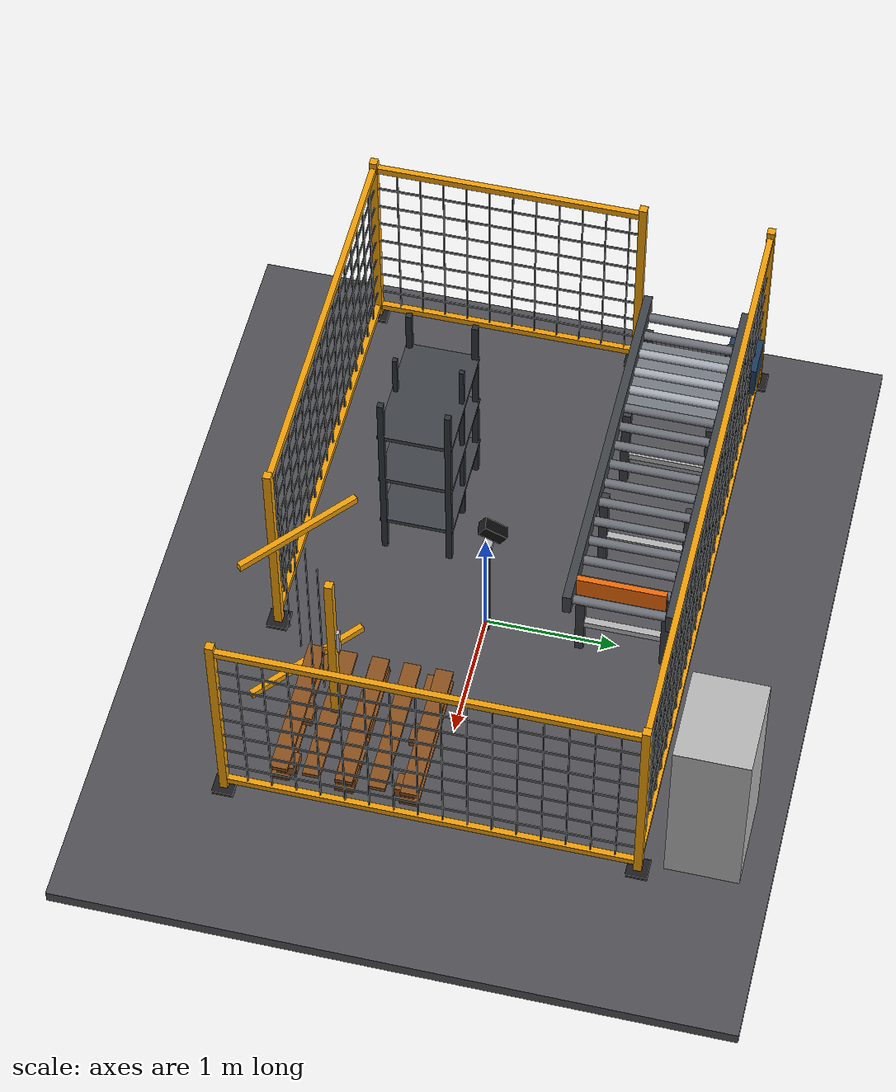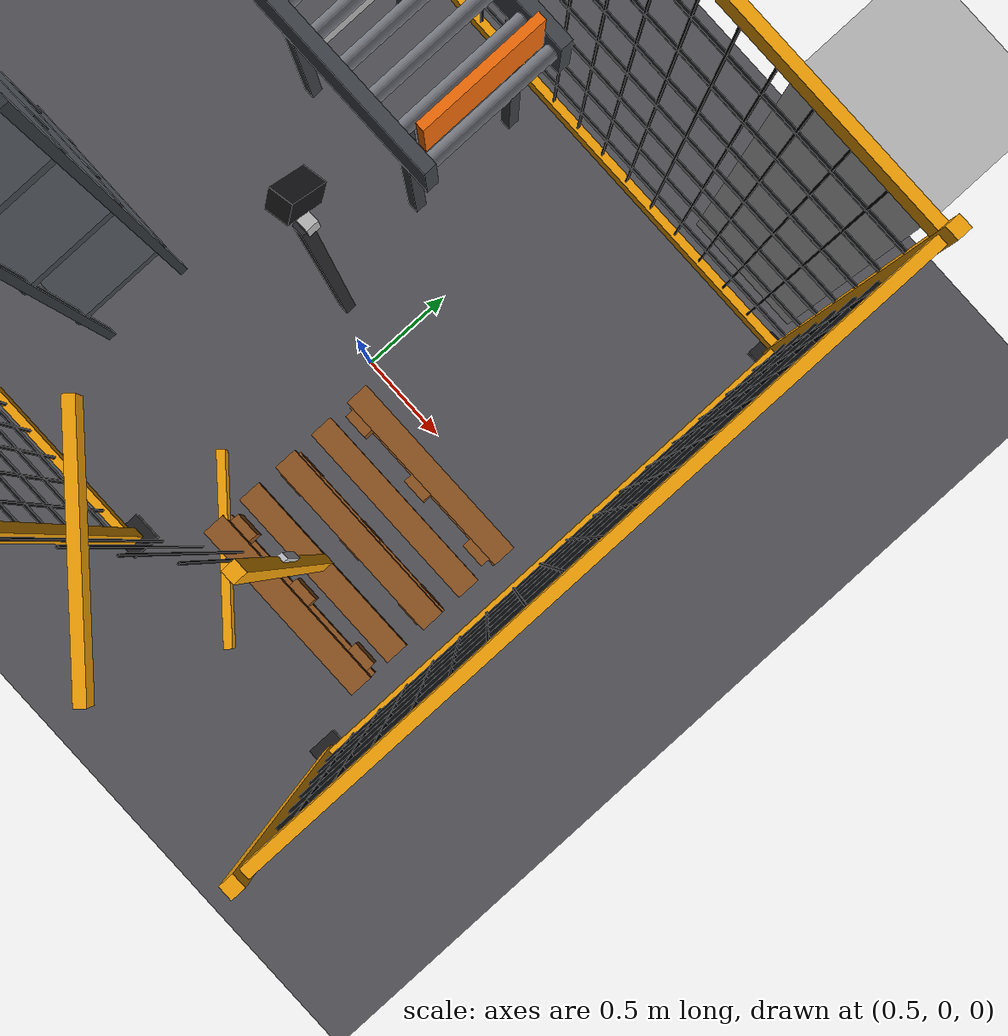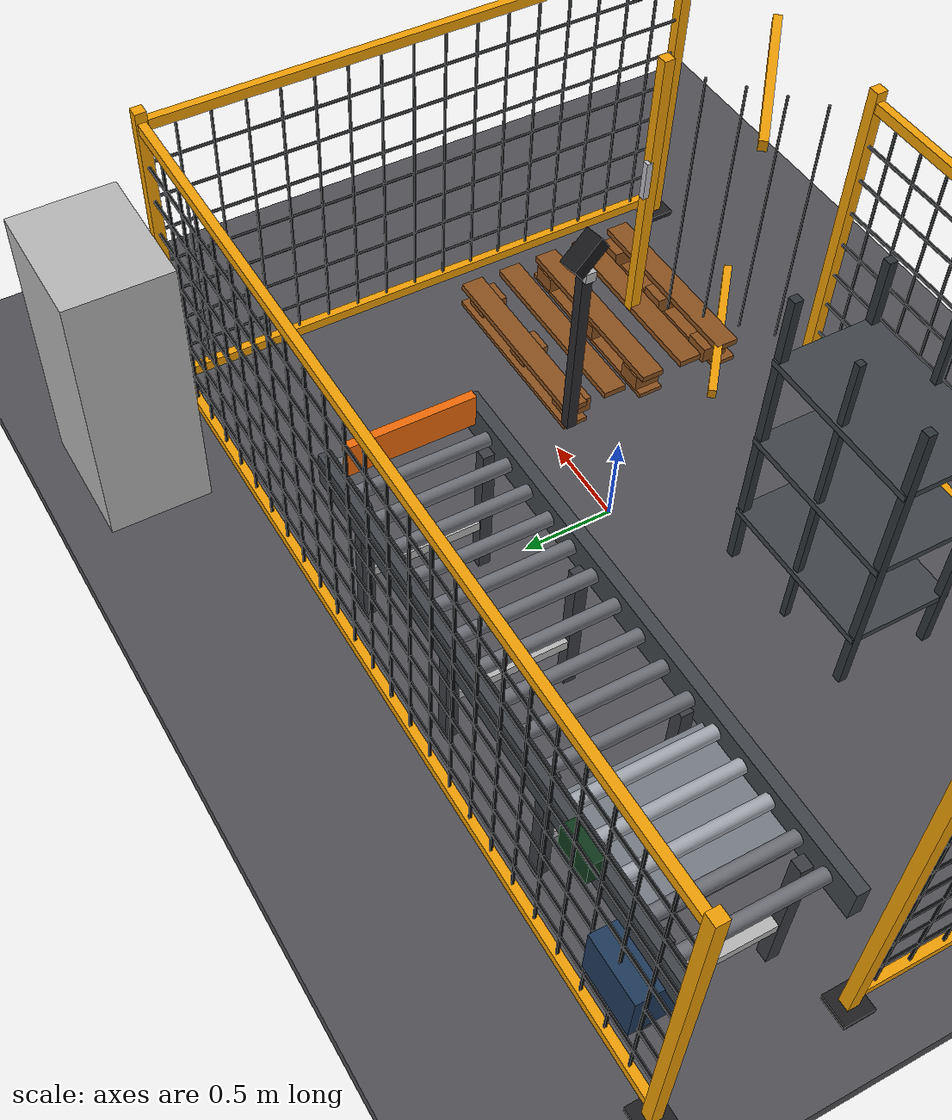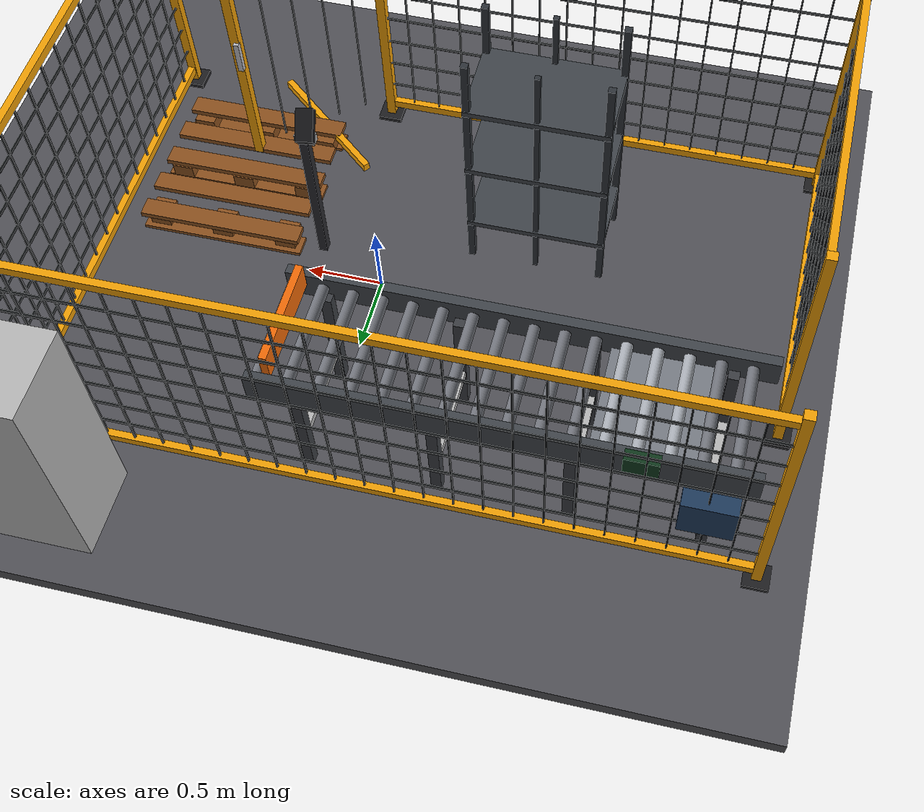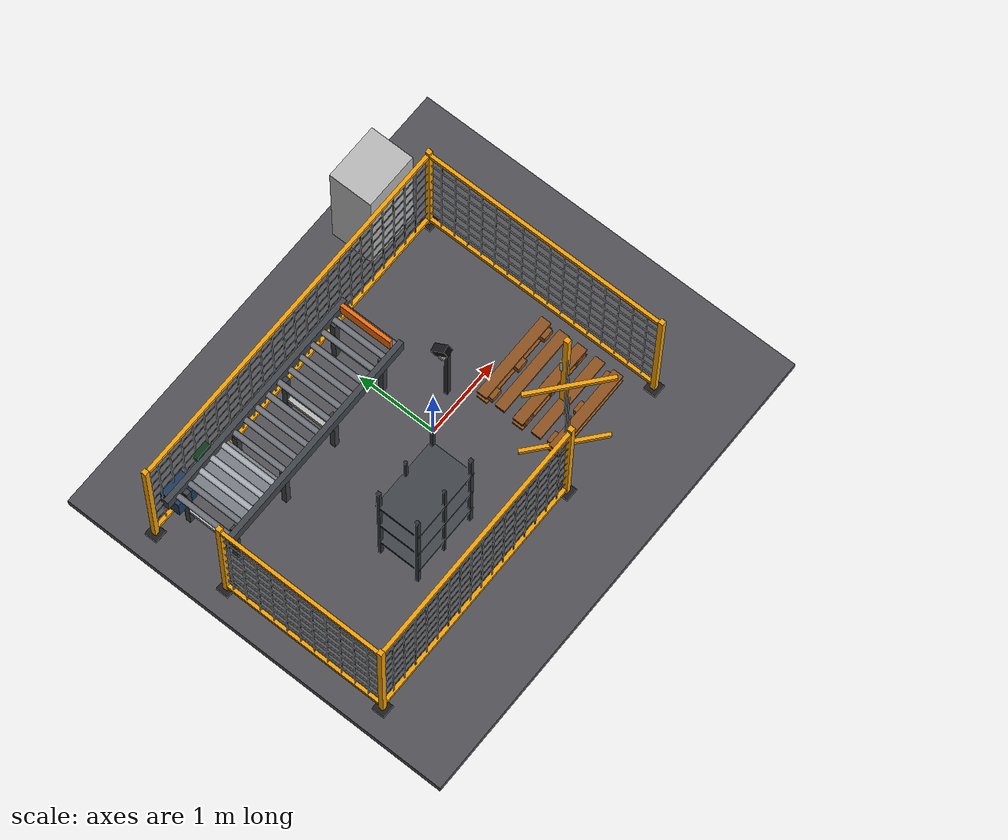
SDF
<?xml version="1.0"?>
<sdf version="1.8">
  <world name="ahead_workcell_v3_2_fence">
    <plugin filename="ignition-gazebo-physics-system" name="ignition::gazebo::systems::Physics"/>
    <plugin filename="ignition-gazebo-user-commands-system" name="ignition::gazebo::systems::UserCommands"/>
    <plugin filename="ignition-gazebo-scene-broadcaster-system" name="ignition::gazebo::systems::SceneBroadcaster"/>
    <plugin filename="ignition-gazebo-sensors-system" name="ignition::gazebo::systems::Sensors"><render_engine>ogre2</render_engine></plugin>
    <gravity>0 0 -9.80665</gravity>
    <physics name="default_physics" type="ignored"><max_step_size>0.001</max_step_size><real_time_factor>1.0</real_time_factor></physics>
    <light type="directional" name="sun"><pose>0 0 8 0 0 0</pose><diffuse>0.8 0.8 0.8 1</diffuse><direction>-0.4 0.3 -1</direction></light>

    <model name="floor"><static>true</static><link name="floor_link">
      <collision name="collision"><pose>0 0 -0.05 0 0 0</pose><geometry><box><size>6 5 0.10</size></box></geometry></collision>
      <visual name="visual"><pose>0 0 -0.05 0 0 0</pose><geometry><box><size>6 5 0.10</size></box></geometry><material><ambient>0.22 0.22 0.23 1</ambient><diffuse>0.32 0.32 0.34 1</diffuse></material></visual>
    </link></model>

    <model name="conveyor_main">
      <static>true</static>

      <link name="conveyor_link">

        <collision name="collision">
          <pose>-1.15 1.05 0.75 0 0 0</pose>

          <geometry>
            <box><size>2.80 0.80 0.20</size></box>
          </geometry>

          <surface>
            <friction>
              <ode>
                <mu>0.7</mu>
                <mu2>150</mu2>
                <fdir1>0 1 0</fdir1>
              </ode>
            </friction>
          </surface>
        </collision>

        <!-- aluminium / steel side frame -->
        <visual name="left_rail">
          <pose>-1.15 0.67 0.84 0 0 0</pose>
          <geometry>
            <box><size>2.90 0.065 0.18</size></box>
          </geometry>
          <material>
            <ambient>0.11 0.12 0.13 1</ambient>
            <diffuse>0.25 0.27 0.29 1</diffuse>
          </material>
        </visual>

        <visual name="right_rail">
          <pose>-1.15 1.43 0.84 0 0 0</pose>
          <geometry>
            <box><size>2.90 0.065 0.18</size></box>
          </geometry>
          <material>
            <ambient>0.11 0.12 0.13 1</ambient>
            <diffuse>0.25 0.27 0.29 1</diffuse>
          </material>
        </visual>

        <visual name="roller_00">
          <pose>-2.450 1.05 0.86 1.57079632679 0 0</pose>
          <geometry>
            <cylinder>
              <radius>0.035</radius>
              <length>0.68</length>
            </cylinder>
          </geometry>
          <material>
            <ambient>0.27 0.28 0.30 1</ambient>
            <diffuse>0.44 0.45 0.48 1</diffuse>
          </material>
        </visual>

        <visual name="roller_01">
          <pose>-2.270 1.05 0.86 1.57079632679 0 0</pose>
          <geometry>
            <cylinder>
              <radius>0.035</radius>
              <length>0.68</length>
            </cylinder>
          </geometry>
          <material>
            <ambient>0.27 0.28 0.30 1</ambient>
            <diffuse>0.44 0.45 0.48 1</diffuse>
          </material>
        </visual>

        <visual name="roller_02">
          <pose>-2.090 1.05 0.86 1.57079632679 0 0</pose>
          <geometry>
            <cylinder>
              <radius>0.035</radius>
              <length>0.68</length>
            </cylinder>
          </geometry>
          <material>
            <ambient>0.43 0.45 0.47 1</ambient>
            <diffuse>0.66 0.68 0.71 1</diffuse>
          </material>
        </visual>

        <visual name="roller_03">
          <pose>-1.910 1.05 0.86 1.57079632679 0 0</pose>
          <geometry>
            <cylinder>
              <radius>0.035</radius>
              <length>0.68</length>
            </cylinder>
          </geometry>
          <material>
            <ambient>0.43 0.45 0.47 1</ambient>
            <diffuse>0.66 0.68 0.71 1</diffuse>
          </material>
        </visual>

        <visual name="roller_04">
          <pose>-1.730 1.05 0.86 1.57079632679 0 0</pose>
          <geometry>
            <cylinder>
              <radius>0.035</radius>
              <length>0.68</length>
            </cylinder>
          </geometry>
          <material>
            <ambient>0.43 0.45 0.47 1</ambient>
            <diffuse>0.66 0.68 0.71 1</diffuse>
          </material>
        </visual>

        <visual name="roller_05">
          <pose>-1.550 1.05 0.86 1.57079632679 0 0</pose>
          <geometry>
            <cylinder>
              <radius>0.035</radius>
              <length>0.68</length>
            </cylinder>
          </geometry>
          <material>
            <ambient>0.27 0.28 0.30 1</ambient>
            <diffuse>0.44 0.45 0.48 1</diffuse>
          </material>
        </visual>

        <visual name="roller_06">
          <pose>-1.370 1.05 0.86 1.57079632679 0 0</pose>
          <geometry>
            <cylinder>
              <radius>0.035</radius>
              <length>0.68</length>
            </cylinder>
          </geometry>
          <material>
            <ambient>0.27 0.28 0.30 1</ambient>
            <diffuse>0.44 0.45 0.48 1</diffuse>
          </material>
        </visual>

        <visual name="roller_07">
          <pose>-1.190 1.05 0.86 1.57079632679 0 0</pose>
          <geometry>
            <cylinder>
              <radius>0.035</radius>
              <length>0.68</length>
            </cylinder>
          </geometry>
          <material>
            <ambient>0.27 0.28 0.30 1</ambient>
            <diffuse>0.44 0.45 0.48 1</diffuse>
          </material>
        </visual>

        <visual name="roller_08">
          <pose>-1.010 1.05 0.86 1.57079632679 0 0</pose>
          <geometry>
            <cylinder>
              <radius>0.035</radius>
              <length>0.68</length>
            </cylinder>
          </geometry>
          <material>
            <ambient>0.27 0.28 0.30 1</ambient>
            <diffuse>0.44 0.45 0.48 1</diffuse>
          </material>
        </visual>

        <visual name="roller_09">
          <pose>-0.830 1.05 0.86 1.57079632679 0 0</pose>
          <geometry>
            <cylinder>
              <radius>0.035</radius>
              <length>0.68</length>
            </cylinder>
          </geometry>
          <material>
            <ambient>0.27 0.28 0.30 1</ambient>
            <diffuse>0.44 0.45 0.48 1</diffuse>
          </material>
        </visual>

        <visual name="roller_10">
          <pose>-0.650 1.05 0.86 1.57079632679 0 0</pose>
          <geometry>
            <cylinder>
              <radius>0.035</radius>
              <length>0.68</length>
            </cylinder>
          </geometry>
          <material>
            <ambient>0.27 0.28 0.30 1</ambient>
            <diffuse>0.44 0.45 0.48 1</diffuse>
          </material>
        </visual>

        <visual name="roller_11">
          <pose>-0.470 1.05 0.86 1.57079632679 0 0</pose>
          <geometry>
            <cylinder>
              <radius>0.035</radius>
              <length>0.68</length>
            </cylinder>
          </geometry>
          <material>
            <ambient>0.27 0.28 0.30 1</ambient>
            <diffuse>0.44 0.45 0.48 1</diffuse>
          </material>
        </visual>

        <visual name="roller_12">
          <pose>-0.290 1.05 0.86 1.57079632679 0 0</pose>
          <geometry>
            <cylinder>
              <radius>0.035</radius>
              <length>0.68</length>
            </cylinder>
          </geometry>
          <material>
            <ambient>0.27 0.28 0.30 1</ambient>
            <diffuse>0.44 0.45 0.48 1</diffuse>
          </material>
        </visual>

        <visual name="roller_13">
          <pose>-0.110 1.05 0.86 1.57079632679 0 0</pose>
          <geometry>
            <cylinder>
              <radius>0.035</radius>
              <length>0.68</length>
            </cylinder>
          </geometry>
          <material>
            <ambient>0.27 0.28 0.30 1</ambient>
            <diffuse>0.44 0.45 0.48 1</diffuse>
          </material>
        </visual>

        <visual name="roller_14">
          <pose>0.070 1.05 0.86 1.57079632679 0 0</pose>
          <geometry>
            <cylinder>
              <radius>0.035</radius>
              <length>0.68</length>
            </cylinder>
          </geometry>
          <material>
            <ambient>0.27 0.28 0.30 1</ambient>
            <diffuse>0.44 0.45 0.48 1</diffuse>
          </material>
        </visual>

        <visual name="roller_15">
          <pose>0.250 1.05 0.86 1.57079632679 0 0</pose>
          <geometry>
            <cylinder>
              <radius>0.035</radius>
              <length>0.68</length>
            </cylinder>
          </geometry>
          <material>
            <ambient>0.27 0.28 0.30 1</ambient>
            <diffuse>0.44 0.45 0.48 1</diffuse>
          </material>
        </visual>

        <visual name="leg_l_0">
          <pose>-2.35 0.73 0.40 0 0 0</pose>
          <geometry>
            <box><size>0.065 0.065 0.80</size></box>
          </geometry>
          <material>
            <ambient>0.12 0.13 0.14 1</ambient>
            <diffuse>0.23 0.24 0.26 1</diffuse>
          </material>
        </visual>

        <visual name="leg_r_0">
          <pose>-2.35 1.37 0.40 0 0 0</pose>
          <geometry>
            <box><size>0.065 0.065 0.80</size></box>
          </geometry>
          <material>
            <ambient>0.12 0.13 0.14 1</ambient>
            <diffuse>0.23 0.24 0.26 1</diffuse>
          </material>
        </visual>

        <visual name="crossbar_0">
          <pose>-2.35 1.05 0.31 0 0 0</pose>
          <geometry>
            <box><size>0.055 0.68 0.055</size></box>
          </geometry>
        </visual>

        <visual name="leg_l_1">
          <pose>-1.55 0.73 0.40 0 0 0</pose>
          <geometry>
            <box><size>0.065 0.065 0.80</size></box>
          </geometry>
          <material>
            <ambient>0.12 0.13 0.14 1</ambient>
            <diffuse>0.23 0.24 0.26 1</diffuse>
          </material>
        </visual>

        <visual name="leg_r_1">
          <pose>-1.55 1.37 0.40 0 0 0</pose>
          <geometry>
            <box><size>0.065 0.065 0.80</size></box>
          </geometry>
          <material>
            <ambient>0.12 0.13 0.14 1</ambient>
            <diffuse>0.23 0.24 0.26 1</diffuse>
          </material>
        </visual>

        <visual name="crossbar_1">
          <pose>-1.55 1.05 0.31 0 0 0</pose>
          <geometry>
            <box><size>0.055 0.68 0.055</size></box>
          </geometry>
        </visual>

        <visual name="leg_l_2">
          <pose>-0.75 0.73 0.40 0 0 0</pose>
          <geometry>
            <box><size>0.065 0.065 0.80</size></box>
          </geometry>
          <material>
            <ambient>0.12 0.13 0.14 1</ambient>
            <diffuse>0.23 0.24 0.26 1</diffuse>
          </material>
        </visual>

        <visual name="leg_r_2">
          <pose>-0.75 1.37 0.40 0 0 0</pose>
          <geometry>
            <box><size>0.065 0.065 0.80</size></box>
          </geometry>
          <material>
            <ambient>0.12 0.13 0.14 1</ambient>
            <diffuse>0.23 0.24 0.26 1</diffuse>
          </material>
        </visual>

        <visual name="crossbar_2">
          <pose>-0.75 1.05 0.31 0 0 0</pose>
          <geometry>
            <box><size>0.055 0.68 0.055</size></box>
          </geometry>
        </visual>

        <visual name="leg_l_3">
          <pose>0.05 0.73 0.40 0 0 0</pose>
          <geometry>
            <box><size>0.065 0.065 0.80</size></box>
          </geometry>
          <material>
            <ambient>0.12 0.13 0.14 1</ambient>
            <diffuse>0.23 0.24 0.26 1</diffuse>
          </material>
        </visual>

        <visual name="leg_r_3">
          <pose>0.05 1.37 0.40 0 0 0</pose>
          <geometry>
            <box><size>0.065 0.065 0.80</size></box>
          </geometry>
          <material>
            <ambient>0.12 0.13 0.14 1</ambient>
            <diffuse>0.23 0.24 0.26 1</diffuse>
          </material>
        </visual>

        <visual name="crossbar_3">
          <pose>0.05 1.05 0.31 0 0 0</pose>
          <geometry>
            <box><size>0.055 0.68 0.055</size></box>
          </geometry>
        </visual>

        <!-- Motor / drive box -->
        <visual name="drive_motor">
          <pose>-2.35 1.47 0.62 0 0 0</pose>
          <geometry>
            <box><size>0.32 0.25 0.28</size></box>
          </geometry>
          <material>
            <ambient>0.06 0.10 0.15 1</ambient>
            <diffuse>0.12 0.23 0.36 1</diffuse>
          </material>
        </visual>

        <!-- Pick position stopper -->
        <visual name="pick_stopper">
          <pose>0.19 1.05 0.96 0 0 0</pose>
          <geometry>
            <box><size>0.045 0.66 0.18</size></box>
          </geometry>
          <material>
            <ambient>0.65 0.25 0.02 1</ambient>
            <diffuse>0.95 0.42 0.03 1</diffuse>
          </material>
        </visual>

      </link>

      <plugin filename="libignition-gazebo-track-controller-system.so"
              name="gz::sim::systems::TrackController">
        <link>conveyor_link</link>
      </plugin>

    </model>

    <model name="inline_scale">
      <static>true</static>

      <link name="scale_link">

        <visual name="weighing_frame">
          <pose>-1.95 1.05 0.755 0 0 0</pose>
          <geometry>
            <box><size>0.62 0.70 0.085</size></box>
          </geometry>
          <material>
            <ambient>0.24 0.25 0.27 1</ambient>
            <diffuse>0.47 0.49 0.52 1</diffuse>
          </material>
        </visual>

        <visual name="loadcell_base">
          <pose>-1.95 1.05 0.685 0 0 0</pose>
          <geometry>
            <box><size>0.52 0.54 0.045</size></box>
          </geometry>
          <material>
            <ambient>0.08 0.09 0.10 1</ambient>
            <diffuse>0.17 0.18 0.20 1</diffuse>
          </material>
        </visual>

        <!-- Small scale display on side -->
        <visual name="indicator">
          <pose>-1.95 1.49 0.93 0 0 0</pose>
          <geometry>
            <box><size>0.20 0.07 0.14</size></box>
          </geometry>
          <material>
            <ambient>0.03 0.08 0.05 1</ambient>
            <diffuse>0.06 0.22 0.11 1</diffuse>
          </material>
        </visual>

      </link>
    </model>

    <model name="pallet_main">
      <static>true</static>
      <pose>1.15 -0.65 0 0 0 0</pose>
      <link name="pallet_link">

      <collision name="bottom_runner_0_collision">
        <pose>0 -0.48 0.0125 0 0 0</pose>
        <geometry><box><size>1.1 0.14 0.025</size></box></geometry>
      </collision>
      <visual name="bottom_runner_0_visual">
        <pose>0 -0.48 0.0125 0 0 0</pose>
        <geometry><box><size>1.1 0.14 0.025</size></box></geometry>
        <material>
          <ambient>0.34 0.20 0.08 1</ambient>
          <diffuse>0.55 0.32 0.12 1</diffuse>
        </material>
      </visual>

      <collision name="bottom_runner_1_collision">
        <pose>0 0.0 0.0125 0 0 0</pose>
        <geometry><box><size>1.1 0.14 0.025</size></box></geometry>
      </collision>
      <visual name="bottom_runner_1_visual">
        <pose>0 0.0 0.0125 0 0 0</pose>
        <geometry><box><size>1.1 0.14 0.025</size></box></geometry>
        <material>
          <ambient>0.34 0.20 0.08 1</ambient>
          <diffuse>0.55 0.32 0.12 1</diffuse>
        </material>
      </visual>

      <collision name="bottom_runner_2_collision">
        <pose>0 0.48 0.0125 0 0 0</pose>
        <geometry><box><size>1.1 0.14 0.025</size></box></geometry>
      </collision>
      <visual name="bottom_runner_2_visual">
        <pose>0 0.48 0.0125 0 0 0</pose>
        <geometry><box><size>1.1 0.14 0.025</size></box></geometry>
        <material>
          <ambient>0.34 0.20 0.08 1</ambient>
          <diffuse>0.55 0.32 0.12 1</diffuse>
        </material>
      </visual>

      <collision name="support_block_0_0_collision">
        <pose>-0.44 -0.44 0.07 0 0 0</pose>
        <geometry><box><size>0.14 0.15 0.09</size></box></geometry>
      </collision>
      <visual name="support_block_0_0_visual">
        <pose>-0.44 -0.44 0.07 0 0 0</pose>
        <geometry><box><size>0.14 0.15 0.09</size></box></geometry>
        <material>
          <ambient>0.34 0.20 0.08 1</ambient>
          <diffuse>0.55 0.32 0.12 1</diffuse>
        </material>
      </visual>

      <collision name="support_block_0_1_collision">
        <pose>-0.44 0.0 0.07 0 0 0</pose>
        <geometry><box><size>0.14 0.15 0.09</size></box></geometry>
      </collision>
      <visual name="support_block_0_1_visual">
        <pose>-0.44 0.0 0.07 0 0 0</pose>
        <geometry><box><size>0.14 0.15 0.09</size></box></geometry>
        <material>
          <ambient>0.34 0.20 0.08 1</ambient>
          <diffuse>0.55 0.32 0.12 1</diffuse>
        </material>
      </visual>

      <collision name="support_block_0_2_collision">
        <pose>-0.44 0.44 0.07 0 0 0</pose>
        <geometry><box><size>0.14 0.15 0.09</size></box></geometry>
      </collision>
      <visual name="support_block_0_2_visual">
        <pose>-0.44 0.44 0.07 0 0 0</pose>
        <geometry><box><size>0.14 0.15 0.09</size></box></geometry>
        <material>
          <ambient>0.34 0.20 0.08 1</ambient>
          <diffuse>0.55 0.32 0.12 1</diffuse>
        </material>
      </visual>

      <collision name="support_block_1_0_collision">
        <pose>0.0 -0.44 0.07 0 0 0</pose>
        <geometry><box><size>0.14 0.15 0.09</size></box></geometry>
      </collision>
      <visual name="support_block_1_0_visual">
        <pose>0.0 -0.44 0.07 0 0 0</pose>
        <geometry><box><size>0.14 0.15 0.09</size></box></geometry>
        <material>
          <ambient>0.34 0.20 0.08 1</ambient>
          <diffuse>0.55 0.32 0.12 1</diffuse>
        </material>
      </visual>

      <collision name="support_block_1_1_collision">
        <pose>0.0 0.0 0.07 0 0 0</pose>
        <geometry><box><size>0.14 0.15 0.09</size></box></geometry>
      </collision>
      <visual name="support_block_1_1_visual">
        <pose>0.0 0.0 0.07 0 0 0</pose>
        <geometry><box><size>0.14 0.15 0.09</size></box></geometry>
        <material>
          <ambient>0.34 0.20 0.08 1</ambient>
          <diffuse>0.55 0.32 0.12 1</diffuse>
        </material>
      </visual>

      <collision name="support_block_1_2_collision">
        <pose>0.0 0.44 0.07 0 0 0</pose>
        <geometry><box><size>0.14 0.15 0.09</size></box></geometry>
      </collision>
      <visual name="support_block_1_2_visual">
        <pose>0.0 0.44 0.07 0 0 0</pose>
        <geometry><box><size>0.14 0.15 0.09</size></box></geometry>
        <material>
          <ambient>0.34 0.20 0.08 1</ambient>
          <diffuse>0.55 0.32 0.12 1</diffuse>
        </material>
      </visual>

      <collision name="support_block_2_0_collision">
        <pose>0.44 -0.44 0.07 0 0 0</pose>
        <geometry><box><size>0.14 0.15 0.09</size></box></geometry>
      </collision>
      <visual name="support_block_2_0_visual">
        <pose>0.44 -0.44 0.07 0 0 0</pose>
        <geometry><box><size>0.14 0.15 0.09</size></box></geometry>
        <material>
          <ambient>0.34 0.20 0.08 1</ambient>
          <diffuse>0.55 0.32 0.12 1</diffuse>
        </material>
      </visual>

      <collision name="support_block_2_1_collision">
        <pose>0.44 0.0 0.07 0 0 0</pose>
        <geometry><box><size>0.14 0.15 0.09</size></box></geometry>
      </collision>
      <visual name="support_block_2_1_visual">
        <pose>0.44 0.0 0.07 0 0 0</pose>
        <geometry><box><size>0.14 0.15 0.09</size></box></geometry>
        <material>
          <ambient>0.34 0.20 0.08 1</ambient>
          <diffuse>0.55 0.32 0.12 1</diffuse>
        </material>
      </visual>

      <collision name="support_block_2_2_collision">
        <pose>0.44 0.44 0.07 0 0 0</pose>
        <geometry><box><size>0.14 0.15 0.09</size></box></geometry>
      </collision>
      <visual name="support_block_2_2_visual">
        <pose>0.44 0.44 0.07 0 0 0</pose>
        <geometry><box><size>0.14 0.15 0.09</size></box></geometry>
        <material>
          <ambient>0.34 0.20 0.08 1</ambient>
          <diffuse>0.55 0.32 0.12 1</diffuse>
        </material>
      </visual>

      <collision name="top_board_0_collision">
        <pose>0 -0.484 0.1325 0 0 0</pose>
        <geometry><box><size>1.1 0.13 0.035</size></box></geometry>
      </collision>
      <visual name="top_board_0_visual">
        <pose>0 -0.484 0.1325 0 0 0</pose>
        <geometry><box><size>1.1 0.13 0.035</size></box></geometry>
        <material>
          <ambient>0.34 0.20 0.08 1</ambient>
          <diffuse>0.55 0.32 0.12 1</diffuse>
        </material>
      </visual>

      <collision name="top_board_1_collision">
        <pose>0 -0.242 0.1325 0 0 0</pose>
        <geometry><box><size>1.1 0.13 0.035</size></box></geometry>
      </collision>
      <visual name="top_board_1_visual">
        <pose>0 -0.242 0.1325 0 0 0</pose>
        <geometry><box><size>1.1 0.13 0.035</size></box></geometry>
        <material>
          <ambient>0.34 0.20 0.08 1</ambient>
          <diffuse>0.55 0.32 0.12 1</diffuse>
        </material>
      </visual>

      <collision name="top_board_2_collision">
        <pose>0 0.0 0.1325 0 0 0</pose>
        <geometry><box><size>1.1 0.13 0.035</size></box></geometry>
      </collision>
      <visual name="top_board_2_visual">
        <pose>0 0.0 0.1325 0 0 0</pose>
        <geometry><box><size>1.1 0.13 0.035</size></box></geometry>
        <material>
          <ambient>0.34 0.20 0.08 1</ambient>
          <diffuse>0.55 0.32 0.12 1</diffuse>
        </material>
      </visual>

      <collision name="top_board_3_collision">
        <pose>0 0.242 0.1325 0 0 0</pose>
        <geometry><box><size>1.1 0.13 0.035</size></box></geometry>
      </collision>
      <visual name="top_board_3_visual">
        <pose>0 0.242 0.1325 0 0 0</pose>
        <geometry><box><size>1.1 0.13 0.035</size></box></geometry>
        <material>
          <ambient>0.34 0.20 0.08 1</ambient>
          <diffuse>0.55 0.32 0.12 1</diffuse>
        </material>
      </visual>

      <collision name="top_board_4_collision">
        <pose>0 0.484 0.1325 0 0 0</pose>
        <geometry><box><size>1.1 0.13 0.035</size></box></geometry>
      </collision>
      <visual name="top_board_4_visual">
        <pose>0 0.484 0.1325 0 0 0</pose>
        <geometry><box><size>1.1 0.13 0.035</size></box></geometry>
        <material>
          <ambient>0.34 0.20 0.08 1</ambient>
          <diffuse>0.55 0.32 0.12 1</diffuse>
        </material>
      </visual>

      </link>
    </model>

    <model name="buffer_rack">
      <static>true</static>

      <pose>-0.95 -0.65 0 0 0 0</pose>

      <link name="rack_link">

        <collision name="post_fl_collision">
          <pose>-0.43 -0.25 0.85 0 0 0</pose>
          <geometry><box><size>0.045 0.045 1.70</size></box></geometry>
        </collision>

        <visual name="post_fl_visual">
          <pose>-0.43 -0.25 0.85 0 0 0</pose>
          <geometry><box><size>0.045 0.045 1.70</size></box></geometry>
          <material>
            <ambient>0.18 0.20 0.22 1</ambient>
            <diffuse>0.18 0.20 0.22 1</diffuse>
          </material>
        </visual>

        <collision name="post_fr_collision">
          <pose>0.43 -0.25 0.85 0 0 0</pose>
          <geometry><box><size>0.045 0.045 1.70</size></box></geometry>
        </collision>

        <visual name="post_fr_visual">
          <pose>0.43 -0.25 0.85 0 0 0</pose>
          <geometry><box><size>0.045 0.045 1.70</size></box></geometry>
          <material>
            <ambient>0.18 0.20 0.22 1</ambient>
            <diffuse>0.18 0.20 0.22 1</diffuse>
          </material>
        </visual>

        <collision name="post_bl_collision">
          <pose>-0.43 0.25 0.85 0 0 0</pose>
          <geometry><box><size>0.045 0.045 1.70</size></box></geometry>
        </collision>

        <visual name="post_bl_visual">
          <pose>-0.43 0.25 0.85 0 0 0</pose>
          <geometry><box><size>0.045 0.045 1.70</size></box></geometry>
          <material>
            <ambient>0.18 0.20 0.22 1</ambient>
            <diffuse>0.18 0.20 0.22 1</diffuse>
          </material>
        </visual>

        <collision name="post_br_collision">
          <pose>0.43 0.25 0.85 0 0 0</pose>
          <geometry><box><size>0.045 0.045 1.70</size></box></geometry>
        </collision>

        <visual name="post_br_visual">
          <pose>0.43 0.25 0.85 0 0 0</pose>
          <geometry><box><size>0.045 0.045 1.70</size></box></geometry>
          <material>
            <ambient>0.18 0.20 0.22 1</ambient>
            <diffuse>0.18 0.20 0.22 1</diffuse>
          </material>
        </visual>

        <collision name="center_front_collision">
          <pose>0 -0.25 0.85 0 0 0</pose>
          <geometry><box><size>0.035 0.035 1.70</size></box></geometry>
        </collision>

        <visual name="center_front_visual">
          <pose>0 -0.25 0.85 0 0 0</pose>
          <geometry><box><size>0.035 0.035 1.70</size></box></geometry>
          <material>
            <ambient>0.18 0.20 0.22 1</ambient>
            <diffuse>0.18 0.20 0.22 1</diffuse>
          </material>
        </visual>

        <collision name="center_back_collision">
          <pose>0 0.25 0.85 0 0 0</pose>
          <geometry><box><size>0.035 0.035 1.70</size></box></geometry>
        </collision>

        <visual name="center_back_visual">
          <pose>0 0.25 0.85 0 0 0</pose>
          <geometry><box><size>0.035 0.035 1.70</size></box></geometry>
          <material>
            <ambient>0.18 0.20 0.22 1</ambient>
            <diffuse>0.18 0.20 0.22 1</diffuse>
          </material>
        </visual>

        <collision name="shelf_0_collision">
          <pose>0 0 0.33 0 0 0</pose>
          <geometry><box><size>0.90 0.56 0.035</size></box></geometry>
        </collision>

        <visual name="shelf_0_visual">
          <pose>0 0 0.33 0 0 0</pose>
          <geometry><box><size>0.90 0.56 0.035</size></box></geometry>
          <material>
            <ambient>0.25 0.27 0.29 1</ambient>
            <diffuse>0.25 0.27 0.29 1</diffuse>
          </material>
        </visual>

        <collision name="shelf_1_collision">
          <pose>0 0 0.83 0 0 0</pose>
          <geometry><box><size>0.90 0.56 0.035</size></box></geometry>
        </collision>

        <visual name="shelf_1_visual">
          <pose>0 0 0.83 0 0 0</pose>
          <geometry><box><size>0.90 0.56 0.035</size></box></geometry>
          <material>
            <ambient>0.25 0.27 0.29 1</ambient>
            <diffuse>0.25 0.27 0.29 1</diffuse>
          </material>
        </visual>

        <collision name="shelf_2_collision">
          <pose>0 0 1.33 0 0 0</pose>
          <geometry><box><size>0.90 0.56 0.035</size></box></geometry>
        </collision>

        <visual name="shelf_2_visual">
          <pose>0 0 1.33 0 0 0</pose>
          <geometry><box><size>0.90 0.56 0.035</size></box></geometry>
          <material>
            <ambient>0.25 0.27 0.29 1</ambient>
            <diffuse>0.25 0.27 0.29 1</diffuse>
          </material>
        </visual>

      </link>

    </model>

    <model name="camera_1_cctv_base">
      <static>true</static>

      <link name="camera_1_link">

        <visual name="mount_post">
          <pose>0.32 0.08 0.91 0 0 0</pose>
          <geometry>
            <box><size>0.055 0.055 1.02</size></box>
          </geometry>
          <material>
            <ambient>0.08 0.08 0.09 1</ambient>
            <diffuse>0.16 0.16 0.18 1</diffuse>
          </material>
        </visual>

        <visual name="mount_arm">
          <pose>0.30 0.10 1.43 0 0 0</pose>
          <geometry>
            <box><size>0.12 0.055 0.055</size></box>
          </geometry>
        </visual>

        <visual name="camera_housing">
          <pose>0.28 0.12 1.55
                0 0.629544 1.761981</pose>
          <geometry>
            <box><size>0.19 0.10 0.09</size></box>
          </geometry>
          <material>
            <ambient>0.035 0.035 0.04 1</ambient>
            <diffuse>0.08 0.08 0.09 1</diffuse>
          </material>
        </visual>

        <sensor name="cctv_camera_1" type="camera">

          <pose>0.28 0.12 1.55
                0 0.629544 1.761981</pose>

          <always_on>true</always_on>
          <update_rate>15</update_rate>

          <!-- 기존 perception 호환성 유지 -->
          <topic>/pac/top_camera/image</topic>

          <camera>
            <horizontal_fov>1.40</horizontal_fov>

            <image>
              <width>1280</width>
              <height>720</height>
              <format>R8G8B8</format>
            </image>

            <clip>
              <near>0.08</near>
              <far>6.0</far>
            </clip>

          </camera>
        </sensor>

      </link>
    </model>

    <model name="safety_fence">
      <static>true</static>

      <link name="fence_link">

        <collision name="north_panel_collision">
          <pose>-0.425 1.550 0.90 0 0 0</pose>
          <geometry>
            <box><size>4.550 0.025 1.80</size></box>
          </geometry>
        </collision>

        <visual name="north_panel_bottom">
          <pose>-0.425 1.550 0.120 0 0 0</pose>
          <geometry>
            <box><size>4.550 0.045 0.055</size></box>
          </geometry>
          <material>
            <ambient>0.95 0.63 0.02 1</ambient>
            <diffuse>0.95 0.63 0.02 1</diffuse>
          </material>
        </visual>

        <visual name="north_panel_top">
          <pose>-0.425 1.550 1.720 0 0 0</pose>
          <geometry>
            <box><size>4.550 0.045 0.055</size></box>
          </geometry>
          <material>
            <ambient>0.95 0.63 0.02 1</ambient>
            <diffuse>0.95 0.63 0.02 1</diffuse>
          </material>
        </visual>

        <visual name="north_panel_mesh_v_0">
          <pose>-2.520 1.550 0.92 0 0 0</pose>
          <geometry>
            <box><size>0.010 0.014 1.55</size></box>
          </geometry>
          <material>
            <ambient>0.035 0.040 0.045 1</ambient>
            <diffuse>0.035 0.040 0.045 1</diffuse>
          </material>
        </visual>

        <visual name="north_panel_mesh_v_1">
          <pose>-2.340 1.550 0.92 0 0 0</pose>
          <geometry>
            <box><size>0.010 0.014 1.55</size></box>
          </geometry>
          <material>
            <ambient>0.035 0.040 0.045 1</ambient>
            <diffuse>0.035 0.040 0.045 1</diffuse>
          </material>
        </visual>

        <visual name="north_panel_mesh_v_2">
          <pose>-2.160 1.550 0.92 0 0 0</pose>
          <geometry>
            <box><size>0.010 0.014 1.55</size></box>
          </geometry>
          <material>
            <ambient>0.035 0.040 0.045 1</ambient>
            <diffuse>0.035 0.040 0.045 1</diffuse>
          </material>
        </visual>

        <visual name="north_panel_mesh_v_3">
          <pose>-1.980 1.550 0.92 0 0 0</pose>
          <geometry>
            <box><size>0.010 0.014 1.55</size></box>
          </geometry>
          <material>
            <ambient>0.035 0.040 0.045 1</ambient>
            <diffuse>0.035 0.040 0.045 1</diffuse>
          </material>
        </visual>

        <visual name="north_panel_mesh_v_4">
          <pose>-1.800 1.550 0.92 0 0 0</pose>
          <geometry>
            <box><size>0.010 0.014 1.55</size></box>
          </geometry>
          <material>
            <ambient>0.035 0.040 0.045 1</ambient>
            <diffuse>0.035 0.040 0.045 1</diffuse>
          </material>
        </visual>

        <visual name="north_panel_mesh_v_5">
          <pose>-1.620 1.550 0.92 0 0 0</pose>
          <geometry>
            <box><size>0.010 0.014 1.55</size></box>
          </geometry>
          <material>
            <ambient>0.035 0.040 0.045 1</ambient>
            <diffuse>0.035 0.040 0.045 1</diffuse>
          </material>
        </visual>

        <visual name="north_panel_mesh_v_6">
          <pose>-1.440 1.550 0.92 0 0 0</pose>
          <geometry>
            <box><size>0.010 0.014 1.55</size></box>
          </geometry>
          <material>
            <ambient>0.035 0.040 0.045 1</ambient>
            <diffuse>0.035 0.040 0.045 1</diffuse>
          </material>
        </visual>

        <visual name="north_panel_mesh_v_7">
          <pose>-1.260 1.550 0.92 0 0 0</pose>
          <geometry>
            <box><size>0.010 0.014 1.55</size></box>
          </geometry>
          <material>
            <ambient>0.035 0.040 0.045 1</ambient>
            <diffuse>0.035 0.040 0.045 1</diffuse>
          </material>
        </visual>

        <visual name="north_panel_mesh_v_8">
          <pose>-1.080 1.550 0.92 0 0 0</pose>
          <geometry>
            <box><size>0.010 0.014 1.55</size></box>
          </geometry>
          <material>
            <ambient>0.035 0.040 0.045 1</ambient>
            <diffuse>0.035 0.040 0.045 1</diffuse>
          </material>
        </visual>

        <visual name="north_panel_mesh_v_9">
          <pose>-0.900 1.550 0.92 0 0 0</pose>
          <geometry>
            <box><size>0.010 0.014 1.55</size></box>
          </geometry>
          <material>
            <ambient>0.035 0.040 0.045 1</ambient>
            <diffuse>0.035 0.040 0.045 1</diffuse>
          </material>
        </visual>

        <visual name="north_panel_mesh_v_10">
          <pose>-0.720 1.550 0.92 0 0 0</pose>
          <geometry>
            <box><size>0.010 0.014 1.55</size></box>
          </geometry>
          <material>
            <ambient>0.035 0.040 0.045 1</ambient>
            <diffuse>0.035 0.040 0.045 1</diffuse>
          </material>
        </visual>

        <visual name="north_panel_mesh_v_11">
          <pose>-0.540 1.550 0.92 0 0 0</pose>
          <geometry>
            <box><size>0.010 0.014 1.55</size></box>
          </geometry>
          <material>
            <ambient>0.035 0.040 0.045 1</ambient>
            <diffuse>0.035 0.040 0.045 1</diffuse>
          </material>
        </visual>

        <visual name="north_panel_mesh_v_12">
          <pose>-0.360 1.550 0.92 0 0 0</pose>
          <geometry>
            <box><size>0.010 0.014 1.55</size></box>
          </geometry>
          <material>
            <ambient>0.035 0.040 0.045 1</ambient>
            <diffuse>0.035 0.040 0.045 1</diffuse>
          </material>
        </visual>

        <visual name="north_panel_mesh_v_13">
          <pose>-0.180 1.550 0.92 0 0 0</pose>
          <geometry>
            <box><size>0.010 0.014 1.55</size></box>
          </geometry>
          <material>
            <ambient>0.035 0.040 0.045 1</ambient>
            <diffuse>0.035 0.040 0.045 1</diffuse>
          </material>
        </visual>

        <visual name="north_panel_mesh_v_14">
          <pose>-0.000 1.550 0.92 0 0 0</pose>
          <geometry>
            <box><size>0.010 0.014 1.55</size></box>
          </geometry>
          <material>
            <ambient>0.035 0.040 0.045 1</ambient>
            <diffuse>0.035 0.040 0.045 1</diffuse>
          </material>
        </visual>

        <visual name="north_panel_mesh_v_15">
          <pose>0.180 1.550 0.92 0 0 0</pose>
          <geometry>
            <box><size>0.010 0.014 1.55</size></box>
          </geometry>
          <material>
            <ambient>0.035 0.040 0.045 1</ambient>
            <diffuse>0.035 0.040 0.045 1</diffuse>
          </material>
        </visual>

        <visual name="north_panel_mesh_v_16">
          <pose>0.360 1.550 0.92 0 0 0</pose>
          <geometry>
            <box><size>0.010 0.014 1.55</size></box>
          </geometry>
          <material>
            <ambient>0.035 0.040 0.045 1</ambient>
            <diffuse>0.035 0.040 0.045 1</diffuse>
          </material>
        </visual>

        <visual name="north_panel_mesh_v_17">
          <pose>0.540 1.550 0.92 0 0 0</pose>
          <geometry>
            <box><size>0.010 0.014 1.55</size></box>
          </geometry>
          <material>
            <ambient>0.035 0.040 0.045 1</ambient>
            <diffuse>0.035 0.040 0.045 1</diffuse>
          </material>
        </visual>

        <visual name="north_panel_mesh_v_18">
          <pose>0.720 1.550 0.92 0 0 0</pose>
          <geometry>
            <box><size>0.010 0.014 1.55</size></box>
          </geometry>
          <material>
            <ambient>0.035 0.040 0.045 1</ambient>
            <diffuse>0.035 0.040 0.045 1</diffuse>
          </material>
        </visual>

        <visual name="north_panel_mesh_v_19">
          <pose>0.900 1.550 0.92 0 0 0</pose>
          <geometry>
            <box><size>0.010 0.014 1.55</size></box>
          </geometry>
          <material>
            <ambient>0.035 0.040 0.045 1</ambient>
            <diffuse>0.035 0.040 0.045 1</diffuse>
          </material>
        </visual>

        <visual name="north_panel_mesh_v_20">
          <pose>1.080 1.550 0.92 0 0 0</pose>
          <geometry>
            <box><size>0.010 0.014 1.55</size></box>
          </geometry>
          <material>
            <ambient>0.035 0.040 0.045 1</ambient>
            <diffuse>0.035 0.040 0.045 1</diffuse>
          </material>
        </visual>

        <visual name="north_panel_mesh_v_21">
          <pose>1.260 1.550 0.92 0 0 0</pose>
          <geometry>
            <box><size>0.010 0.014 1.55</size></box>
          </geometry>
          <material>
            <ambient>0.035 0.040 0.045 1</ambient>
            <diffuse>0.035 0.040 0.045 1</diffuse>
          </material>
        </visual>

        <visual name="north_panel_mesh_v_22">
          <pose>1.440 1.550 0.92 0 0 0</pose>
          <geometry>
            <box><size>0.010 0.014 1.55</size></box>
          </geometry>
          <material>
            <ambient>0.035 0.040 0.045 1</ambient>
            <diffuse>0.035 0.040 0.045 1</diffuse>
          </material>
        </visual>

        <visual name="north_panel_mesh_v_23">
          <pose>1.620 1.550 0.92 0 0 0</pose>
          <geometry>
            <box><size>0.010 0.014 1.55</size></box>
          </geometry>
          <material>
            <ambient>0.035 0.040 0.045 1</ambient>
            <diffuse>0.035 0.040 0.045 1</diffuse>
          </material>
        </visual>

        <visual name="north_panel_mesh_h_0">
          <pose>-0.425 1.550 0.300 0 0 0</pose>
          <geometry>
            <box><size>4.550 0.014 0.010</size></box>
          </geometry>
          <material>
            <ambient>0.035 0.040 0.045 1</ambient>
            <diffuse>0.035 0.040 0.045 1</diffuse>
          </material>
        </visual>

        <visual name="north_panel_mesh_h_1">
          <pose>-0.425 1.550 0.500 0 0 0</pose>
          <geometry>
            <box><size>4.550 0.014 0.010</size></box>
          </geometry>
          <material>
            <ambient>0.035 0.040 0.045 1</ambient>
            <diffuse>0.035 0.040 0.045 1</diffuse>
          </material>
        </visual>

        <visual name="north_panel_mesh_h_2">
          <pose>-0.425 1.550 0.700 0 0 0</pose>
          <geometry>
            <box><size>4.550 0.014 0.010</size></box>
          </geometry>
          <material>
            <ambient>0.035 0.040 0.045 1</ambient>
            <diffuse>0.035 0.040 0.045 1</diffuse>
          </material>
        </visual>

        <visual name="north_panel_mesh_h_3">
          <pose>-0.425 1.550 0.900 0 0 0</pose>
          <geometry>
            <box><size>4.550 0.014 0.010</size></box>
          </geometry>
          <material>
            <ambient>0.035 0.040 0.045 1</ambient>
            <diffuse>0.035 0.040 0.045 1</diffuse>
          </material>
        </visual>

        <visual name="north_panel_mesh_h_4">
          <pose>-0.425 1.550 1.100 0 0 0</pose>
          <geometry>
            <box><size>4.550 0.014 0.010</size></box>
          </geometry>
          <material>
            <ambient>0.035 0.040 0.045 1</ambient>
            <diffuse>0.035 0.040 0.045 1</diffuse>
          </material>
        </visual>

        <visual name="north_panel_mesh_h_5">
          <pose>-0.425 1.550 1.300 0 0 0</pose>
          <geometry>
            <box><size>4.550 0.014 0.010</size></box>
          </geometry>
          <material>
            <ambient>0.035 0.040 0.045 1</ambient>
            <diffuse>0.035 0.040 0.045 1</diffuse>
          </material>
        </visual>

        <visual name="north_panel_mesh_h_6">
          <pose>-0.425 1.550 1.500 0 0 0</pose>
          <geometry>
            <box><size>4.550 0.014 0.010</size></box>
          </geometry>
          <material>
            <ambient>0.035 0.040 0.045 1</ambient>
            <diffuse>0.035 0.040 0.045 1</diffuse>
          </material>
        </visual>

        <collision name="east_panel_collision">
          <pose>1.850 0.025 0.90 0 0 0</pose>
          <geometry>
            <box><size>0.025 3.050 1.80</size></box>
          </geometry>
        </collision>

        <visual name="east_panel_bottom">
          <pose>1.850 0.025 0.120 0 0 0</pose>
          <geometry>
            <box><size>0.045 3.050 0.055</size></box>
          </geometry>
          <material>
            <ambient>0.95 0.63 0.02 1</ambient>
            <diffuse>0.95 0.63 0.02 1</diffuse>
          </material>
        </visual>

        <visual name="east_panel_top">
          <pose>1.850 0.025 1.720 0 0 0</pose>
          <geometry>
            <box><size>0.045 3.050 0.055</size></box>
          </geometry>
          <material>
            <ambient>0.95 0.63 0.02 1</ambient>
            <diffuse>0.95 0.63 0.02 1</diffuse>
          </material>
        </visual>

        <visual name="east_panel_mesh_v_0">
          <pose>1.850 -1.320 0.92 0 0 0</pose>
          <geometry>
            <box><size>0.014 0.010 1.55</size></box>
          </geometry>
          <material>
            <ambient>0.035 0.040 0.045 1</ambient>
            <diffuse>0.035 0.040 0.045 1</diffuse>
          </material>
        </visual>

        <visual name="east_panel_mesh_v_1">
          <pose>1.850 -1.140 0.92 0 0 0</pose>
          <geometry>
            <box><size>0.014 0.010 1.55</size></box>
          </geometry>
          <material>
            <ambient>0.035 0.040 0.045 1</ambient>
            <diffuse>0.035 0.040 0.045 1</diffuse>
          </material>
        </visual>

        <visual name="east_panel_mesh_v_2">
          <pose>1.850 -0.960 0.92 0 0 0</pose>
          <geometry>
            <box><size>0.014 0.010 1.55</size></box>
          </geometry>
          <material>
            <ambient>0.035 0.040 0.045 1</ambient>
            <diffuse>0.035 0.040 0.045 1</diffuse>
          </material>
        </visual>

        <visual name="east_panel_mesh_v_3">
          <pose>1.850 -0.780 0.92 0 0 0</pose>
          <geometry>
            <box><size>0.014 0.010 1.55</size></box>
          </geometry>
          <material>
            <ambient>0.035 0.040 0.045 1</ambient>
            <diffuse>0.035 0.040 0.045 1</diffuse>
          </material>
        </visual>

        <visual name="east_panel_mesh_v_4">
          <pose>1.850 -0.600 0.92 0 0 0</pose>
          <geometry>
            <box><size>0.014 0.010 1.55</size></box>
          </geometry>
          <material>
            <ambient>0.035 0.040 0.045 1</ambient>
            <diffuse>0.035 0.040 0.045 1</diffuse>
          </material>
        </visual>

        <visual name="east_panel_mesh_v_5">
          <pose>1.850 -0.420 0.92 0 0 0</pose>
          <geometry>
            <box><size>0.014 0.010 1.55</size></box>
          </geometry>
          <material>
            <ambient>0.035 0.040 0.045 1</ambient>
            <diffuse>0.035 0.040 0.045 1</diffuse>
          </material>
        </visual>

        <visual name="east_panel_mesh_v_6">
          <pose>1.850 -0.240 0.92 0 0 0</pose>
          <geometry>
            <box><size>0.014 0.010 1.55</size></box>
          </geometry>
          <material>
            <ambient>0.035 0.040 0.045 1</ambient>
            <diffuse>0.035 0.040 0.045 1</diffuse>
          </material>
        </visual>

        <visual name="east_panel_mesh_v_7">
          <pose>1.850 -0.060 0.92 0 0 0</pose>
          <geometry>
            <box><size>0.014 0.010 1.55</size></box>
          </geometry>
          <material>
            <ambient>0.035 0.040 0.045 1</ambient>
            <diffuse>0.035 0.040 0.045 1</diffuse>
          </material>
        </visual>

        <visual name="east_panel_mesh_v_8">
          <pose>1.850 0.120 0.92 0 0 0</pose>
          <geometry>
            <box><size>0.014 0.010 1.55</size></box>
          </geometry>
          <material>
            <ambient>0.035 0.040 0.045 1</ambient>
            <diffuse>0.035 0.040 0.045 1</diffuse>
          </material>
        </visual>

        <visual name="east_panel_mesh_v_9">
          <pose>1.850 0.300 0.92 0 0 0</pose>
          <geometry>
            <box><size>0.014 0.010 1.55</size></box>
          </geometry>
          <material>
            <ambient>0.035 0.040 0.045 1</ambient>
            <diffuse>0.035 0.040 0.045 1</diffuse>
          </material>
        </visual>

        <visual name="east_panel_mesh_v_10">
          <pose>1.850 0.480 0.92 0 0 0</pose>
          <geometry>
            <box><size>0.014 0.010 1.55</size></box>
          </geometry>
          <material>
            <ambient>0.035 0.040 0.045 1</ambient>
            <diffuse>0.035 0.040 0.045 1</diffuse>
          </material>
        </visual>

        <visual name="east_panel_mesh_v_11">
          <pose>1.850 0.660 0.92 0 0 0</pose>
          <geometry>
            <box><size>0.014 0.010 1.55</size></box>
          </geometry>
          <material>
            <ambient>0.035 0.040 0.045 1</ambient>
            <diffuse>0.035 0.040 0.045 1</diffuse>
          </material>
        </visual>

        <visual name="east_panel_mesh_v_12">
          <pose>1.850 0.840 0.92 0 0 0</pose>
          <geometry>
            <box><size>0.014 0.010 1.55</size></box>
          </geometry>
          <material>
            <ambient>0.035 0.040 0.045 1</ambient>
            <diffuse>0.035 0.040 0.045 1</diffuse>
          </material>
        </visual>

        <visual name="east_panel_mesh_v_13">
          <pose>1.850 1.020 0.92 0 0 0</pose>
          <geometry>
            <box><size>0.014 0.010 1.55</size></box>
          </geometry>
          <material>
            <ambient>0.035 0.040 0.045 1</ambient>
            <diffuse>0.035 0.040 0.045 1</diffuse>
          </material>
        </visual>

        <visual name="east_panel_mesh_v_14">
          <pose>1.850 1.200 0.92 0 0 0</pose>
          <geometry>
            <box><size>0.014 0.010 1.55</size></box>
          </geometry>
          <material>
            <ambient>0.035 0.040 0.045 1</ambient>
            <diffuse>0.035 0.040 0.045 1</diffuse>
          </material>
        </visual>

        <visual name="east_panel_mesh_v_15">
          <pose>1.850 1.380 0.92 0 0 0</pose>
          <geometry>
            <box><size>0.014 0.010 1.55</size></box>
          </geometry>
          <material>
            <ambient>0.035 0.040 0.045 1</ambient>
            <diffuse>0.035 0.040 0.045 1</diffuse>
          </material>
        </visual>

        <visual name="east_panel_mesh_h_0">
          <pose>1.850 0.025 0.300 0 0 0</pose>
          <geometry>
            <box><size>0.014 3.050 0.010</size></box>
          </geometry>
          <material>
            <ambient>0.035 0.040 0.045 1</ambient>
            <diffuse>0.035 0.040 0.045 1</diffuse>
          </material>
        </visual>

        <visual name="east_panel_mesh_h_1">
          <pose>1.850 0.025 0.500 0 0 0</pose>
          <geometry>
            <box><size>0.014 3.050 0.010</size></box>
          </geometry>
          <material>
            <ambient>0.035 0.040 0.045 1</ambient>
            <diffuse>0.035 0.040 0.045 1</diffuse>
          </material>
        </visual>

        <visual name="east_panel_mesh_h_2">
          <pose>1.850 0.025 0.700 0 0 0</pose>
          <geometry>
            <box><size>0.014 3.050 0.010</size></box>
          </geometry>
          <material>
            <ambient>0.035 0.040 0.045 1</ambient>
            <diffuse>0.035 0.040 0.045 1</diffuse>
          </material>
        </visual>

        <visual name="east_panel_mesh_h_3">
          <pose>1.850 0.025 0.900 0 0 0</pose>
          <geometry>
            <box><size>0.014 3.050 0.010</size></box>
          </geometry>
          <material>
            <ambient>0.035 0.040 0.045 1</ambient>
            <diffuse>0.035 0.040 0.045 1</diffuse>
          </material>
        </visual>

        <visual name="east_panel_mesh_h_4">
          <pose>1.850 0.025 1.100 0 0 0</pose>
          <geometry>
            <box><size>0.014 3.050 0.010</size></box>
          </geometry>
          <material>
            <ambient>0.035 0.040 0.045 1</ambient>
            <diffuse>0.035 0.040 0.045 1</diffuse>
          </material>
        </visual>

        <visual name="east_panel_mesh_h_5">
          <pose>1.850 0.025 1.300 0 0 0</pose>
          <geometry>
            <box><size>0.014 3.050 0.010</size></box>
          </geometry>
          <material>
            <ambient>0.035 0.040 0.045 1</ambient>
            <diffuse>0.035 0.040 0.045 1</diffuse>
          </material>
        </visual>

        <visual name="east_panel_mesh_h_6">
          <pose>1.850 0.025 1.500 0 0 0</pose>
          <geometry>
            <box><size>0.014 3.050 0.010</size></box>
          </geometry>
          <material>
            <ambient>0.035 0.040 0.045 1</ambient>
            <diffuse>0.035 0.040 0.045 1</diffuse>
          </material>
        </visual>

        <collision name="west_lower_panel_collision">
          <pose>-2.700 -0.460 0.90 0 0 0</pose>
          <geometry>
            <box><size>0.025 2.080 1.80</size></box>
          </geometry>
        </collision>

        <visual name="west_lower_panel_bottom">
          <pose>-2.700 -0.460 0.120 0 0 0</pose>
          <geometry>
            <box><size>0.045 2.080 0.055</size></box>
          </geometry>
          <material>
            <ambient>0.95 0.63 0.02 1</ambient>
            <diffuse>0.95 0.63 0.02 1</diffuse>
          </material>
        </visual>

        <visual name="west_lower_panel_top">
          <pose>-2.700 -0.460 1.720 0 0 0</pose>
          <geometry>
            <box><size>0.045 2.080 0.055</size></box>
          </geometry>
          <material>
            <ambient>0.95 0.63 0.02 1</ambient>
            <diffuse>0.95 0.63 0.02 1</diffuse>
          </material>
        </visual>

        <visual name="west_lower_panel_mesh_v_0">
          <pose>-2.700 -1.320 0.92 0 0 0</pose>
          <geometry>
            <box><size>0.014 0.010 1.55</size></box>
          </geometry>
          <material>
            <ambient>0.035 0.040 0.045 1</ambient>
            <diffuse>0.035 0.040 0.045 1</diffuse>
          </material>
        </visual>

        <visual name="west_lower_panel_mesh_v_1">
          <pose>-2.700 -1.140 0.92 0 0 0</pose>
          <geometry>
            <box><size>0.014 0.010 1.55</size></box>
          </geometry>
          <material>
            <ambient>0.035 0.040 0.045 1</ambient>
            <diffuse>0.035 0.040 0.045 1</diffuse>
          </material>
        </visual>

        <visual name="west_lower_panel_mesh_v_2">
          <pose>-2.700 -0.960 0.92 0 0 0</pose>
          <geometry>
            <box><size>0.014 0.010 1.55</size></box>
          </geometry>
          <material>
            <ambient>0.035 0.040 0.045 1</ambient>
            <diffuse>0.035 0.040 0.045 1</diffuse>
          </material>
        </visual>

        <visual name="west_lower_panel_mesh_v_3">
          <pose>-2.700 -0.780 0.92 0 0 0</pose>
          <geometry>
            <box><size>0.014 0.010 1.55</size></box>
          </geometry>
          <material>
            <ambient>0.035 0.040 0.045 1</ambient>
            <diffuse>0.035 0.040 0.045 1</diffuse>
          </material>
        </visual>

        <visual name="west_lower_panel_mesh_v_4">
          <pose>-2.700 -0.600 0.92 0 0 0</pose>
          <geometry>
            <box><size>0.014 0.010 1.55</size></box>
          </geometry>
          <material>
            <ambient>0.035 0.040 0.045 1</ambient>
            <diffuse>0.035 0.040 0.045 1</diffuse>
          </material>
        </visual>

        <visual name="west_lower_panel_mesh_v_5">
          <pose>-2.700 -0.420 0.92 0 0 0</pose>
          <geometry>
            <box><size>0.014 0.010 1.55</size></box>
          </geometry>
          <material>
            <ambient>0.035 0.040 0.045 1</ambient>
            <diffuse>0.035 0.040 0.045 1</diffuse>
          </material>
        </visual>

        <visual name="west_lower_panel_mesh_v_6">
          <pose>-2.700 -0.240 0.92 0 0 0</pose>
          <geometry>
            <box><size>0.014 0.010 1.55</size></box>
          </geometry>
          <material>
            <ambient>0.035 0.040 0.045 1</ambient>
            <diffuse>0.035 0.040 0.045 1</diffuse>
          </material>
        </visual>

        <visual name="west_lower_panel_mesh_v_7">
          <pose>-2.700 -0.060 0.92 0 0 0</pose>
          <geometry>
            <box><size>0.014 0.010 1.55</size></box>
          </geometry>
          <material>
            <ambient>0.035 0.040 0.045 1</ambient>
            <diffuse>0.035 0.040 0.045 1</diffuse>
          </material>
        </visual>

        <visual name="west_lower_panel_mesh_v_8">
          <pose>-2.700 0.120 0.92 0 0 0</pose>
          <geometry>
            <box><size>0.014 0.010 1.55</size></box>
          </geometry>
          <material>
            <ambient>0.035 0.040 0.045 1</ambient>
            <diffuse>0.035 0.040 0.045 1</diffuse>
          </material>
        </visual>

        <visual name="west_lower_panel_mesh_v_9">
          <pose>-2.700 0.300 0.92 0 0 0</pose>
          <geometry>
            <box><size>0.014 0.010 1.55</size></box>
          </geometry>
          <material>
            <ambient>0.035 0.040 0.045 1</ambient>
            <diffuse>0.035 0.040 0.045 1</diffuse>
          </material>
        </visual>

        <visual name="west_lower_panel_mesh_v_10">
          <pose>-2.700 0.480 0.92 0 0 0</pose>
          <geometry>
            <box><size>0.014 0.010 1.55</size></box>
          </geometry>
          <material>
            <ambient>0.035 0.040 0.045 1</ambient>
            <diffuse>0.035 0.040 0.045 1</diffuse>
          </material>
        </visual>

        <visual name="west_lower_panel_mesh_h_0">
          <pose>-2.700 -0.460 0.300 0 0 0</pose>
          <geometry>
            <box><size>0.014 2.080 0.010</size></box>
          </geometry>
          <material>
            <ambient>0.035 0.040 0.045 1</ambient>
            <diffuse>0.035 0.040 0.045 1</diffuse>
          </material>
        </visual>

        <visual name="west_lower_panel_mesh_h_1">
          <pose>-2.700 -0.460 0.500 0 0 0</pose>
          <geometry>
            <box><size>0.014 2.080 0.010</size></box>
          </geometry>
          <material>
            <ambient>0.035 0.040 0.045 1</ambient>
            <diffuse>0.035 0.040 0.045 1</diffuse>
          </material>
        </visual>

        <visual name="west_lower_panel_mesh_h_2">
          <pose>-2.700 -0.460 0.700 0 0 0</pose>
          <geometry>
            <box><size>0.014 2.080 0.010</size></box>
          </geometry>
          <material>
            <ambient>0.035 0.040 0.045 1</ambient>
            <diffuse>0.035 0.040 0.045 1</diffuse>
          </material>
        </visual>

        <visual name="west_lower_panel_mesh_h_3">
          <pose>-2.700 -0.460 0.900 0 0 0</pose>
          <geometry>
            <box><size>0.014 2.080 0.010</size></box>
          </geometry>
          <material>
            <ambient>0.035 0.040 0.045 1</ambient>
            <diffuse>0.035 0.040 0.045 1</diffuse>
          </material>
        </visual>

        <visual name="west_lower_panel_mesh_h_4">
          <pose>-2.700 -0.460 1.100 0 0 0</pose>
          <geometry>
            <box><size>0.014 2.080 0.010</size></box>
          </geometry>
          <material>
            <ambient>0.035 0.040 0.045 1</ambient>
            <diffuse>0.035 0.040 0.045 1</diffuse>
          </material>
        </visual>

        <visual name="west_lower_panel_mesh_h_5">
          <pose>-2.700 -0.460 1.300 0 0 0</pose>
          <geometry>
            <box><size>0.014 2.080 0.010</size></box>
          </geometry>
          <material>
            <ambient>0.035 0.040 0.045 1</ambient>
            <diffuse>0.035 0.040 0.045 1</diffuse>
          </material>
        </visual>

        <visual name="west_lower_panel_mesh_h_6">
          <pose>-2.700 -0.460 1.500 0 0 0</pose>
          <geometry>
            <box><size>0.014 2.080 0.010</size></box>
          </geometry>
          <material>
            <ambient>0.035 0.040 0.045 1</ambient>
            <diffuse>0.035 0.040 0.045 1</diffuse>
          </material>
        </visual>

        <collision name="south_left_panel_collision">
          <pose>-1.175 -1.500 0.90 0 0 0</pose>
          <geometry>
            <box><size>3.050 0.025 1.80</size></box>
          </geometry>
        </collision>

        <visual name="south_left_panel_bottom">
          <pose>-1.175 -1.500 0.120 0 0 0</pose>
          <geometry>
            <box><size>3.050 0.045 0.055</size></box>
          </geometry>
          <material>
            <ambient>0.95 0.63 0.02 1</ambient>
            <diffuse>0.95 0.63 0.02 1</diffuse>
          </material>
        </visual>

        <visual name="south_left_panel_top">
          <pose>-1.175 -1.500 1.720 0 0 0</pose>
          <geometry>
            <box><size>3.050 0.045 0.055</size></box>
          </geometry>
          <material>
            <ambient>0.95 0.63 0.02 1</ambient>
            <diffuse>0.95 0.63 0.02 1</diffuse>
          </material>
        </visual>

        <visual name="south_left_panel_mesh_v_0">
          <pose>-2.520 -1.500 0.92 0 0 0</pose>
          <geometry>
            <box><size>0.010 0.014 1.55</size></box>
          </geometry>
          <material>
            <ambient>0.035 0.040 0.045 1</ambient>
            <diffuse>0.035 0.040 0.045 1</diffuse>
          </material>
        </visual>

        <visual name="south_left_panel_mesh_v_1">
          <pose>-2.340 -1.500 0.92 0 0 0</pose>
          <geometry>
            <box><size>0.010 0.014 1.55</size></box>
          </geometry>
          <material>
            <ambient>0.035 0.040 0.045 1</ambient>
            <diffuse>0.035 0.040 0.045 1</diffuse>
          </material>
        </visual>

        <visual name="south_left_panel_mesh_v_2">
          <pose>-2.160 -1.500 0.92 0 0 0</pose>
          <geometry>
            <box><size>0.010 0.014 1.55</size></box>
          </geometry>
          <material>
            <ambient>0.035 0.040 0.045 1</ambient>
            <diffuse>0.035 0.040 0.045 1</diffuse>
          </material>
        </visual>

        <visual name="south_left_panel_mesh_v_3">
          <pose>-1.980 -1.500 0.92 0 0 0</pose>
          <geometry>
            <box><size>0.010 0.014 1.55</size></box>
          </geometry>
          <material>
            <ambient>0.035 0.040 0.045 1</ambient>
            <diffuse>0.035 0.040 0.045 1</diffuse>
          </material>
        </visual>

        <visual name="south_left_panel_mesh_v_4">
          <pose>-1.800 -1.500 0.92 0 0 0</pose>
          <geometry>
            <box><size>0.010 0.014 1.55</size></box>
          </geometry>
          <material>
            <ambient>0.035 0.040 0.045 1</ambient>
            <diffuse>0.035 0.040 0.045 1</diffuse>
          </material>
        </visual>

        <visual name="south_left_panel_mesh_v_5">
          <pose>-1.620 -1.500 0.92 0 0 0</pose>
          <geometry>
            <box><size>0.010 0.014 1.55</size></box>
          </geometry>
          <material>
            <ambient>0.035 0.040 0.045 1</ambient>
            <diffuse>0.035 0.040 0.045 1</diffuse>
          </material>
        </visual>

        <visual name="south_left_panel_mesh_v_6">
          <pose>-1.440 -1.500 0.92 0 0 0</pose>
          <geometry>
            <box><size>0.010 0.014 1.55</size></box>
          </geometry>
          <material>
            <ambient>0.035 0.040 0.045 1</ambient>
            <diffuse>0.035 0.040 0.045 1</diffuse>
          </material>
        </visual>

        <visual name="south_left_panel_mesh_v_7">
          <pose>-1.260 -1.500 0.92 0 0 0</pose>
          <geometry>
            <box><size>0.010 0.014 1.55</size></box>
          </geometry>
          <material>
            <ambient>0.035 0.040 0.045 1</ambient>
            <diffuse>0.035 0.040 0.045 1</diffuse>
          </material>
        </visual>

        <visual name="south_left_panel_mesh_v_8">
          <pose>-1.080 -1.500 0.92 0 0 0</pose>
          <geometry>
            <box><size>0.010 0.014 1.55</size></box>
          </geometry>
          <material>
            <ambient>0.035 0.040 0.045 1</ambient>
            <diffuse>0.035 0.040 0.045 1</diffuse>
          </material>
        </visual>

        <visual name="south_left_panel_mesh_v_9">
          <pose>-0.900 -1.500 0.92 0 0 0</pose>
          <geometry>
            <box><size>0.010 0.014 1.55</size></box>
          </geometry>
          <material>
            <ambient>0.035 0.040 0.045 1</ambient>
            <diffuse>0.035 0.040 0.045 1</diffuse>
          </material>
        </visual>

        <visual name="south_left_panel_mesh_v_10">
          <pose>-0.720 -1.500 0.92 0 0 0</pose>
          <geometry>
            <box><size>0.010 0.014 1.55</size></box>
          </geometry>
          <material>
            <ambient>0.035 0.040 0.045 1</ambient>
            <diffuse>0.035 0.040 0.045 1</diffuse>
          </material>
        </visual>

        <visual name="south_left_panel_mesh_v_11">
          <pose>-0.540 -1.500 0.92 0 0 0</pose>
          <geometry>
            <box><size>0.010 0.014 1.55</size></box>
          </geometry>
          <material>
            <ambient>0.035 0.040 0.045 1</ambient>
            <diffuse>0.035 0.040 0.045 1</diffuse>
          </material>
        </visual>

        <visual name="south_left_panel_mesh_v_12">
          <pose>-0.360 -1.500 0.92 0 0 0</pose>
          <geometry>
            <box><size>0.010 0.014 1.55</size></box>
          </geometry>
          <material>
            <ambient>0.035 0.040 0.045 1</ambient>
            <diffuse>0.035 0.040 0.045 1</diffuse>
          </material>
        </visual>

        <visual name="south_left_panel_mesh_v_13">
          <pose>-0.180 -1.500 0.92 0 0 0</pose>
          <geometry>
            <box><size>0.010 0.014 1.55</size></box>
          </geometry>
          <material>
            <ambient>0.035 0.040 0.045 1</ambient>
            <diffuse>0.035 0.040 0.045 1</diffuse>
          </material>
        </visual>

        <visual name="south_left_panel_mesh_v_14">
          <pose>-0.000 -1.500 0.92 0 0 0</pose>
          <geometry>
            <box><size>0.010 0.014 1.55</size></box>
          </geometry>
          <material>
            <ambient>0.035 0.040 0.045 1</ambient>
            <diffuse>0.035 0.040 0.045 1</diffuse>
          </material>
        </visual>

        <visual name="south_left_panel_mesh_v_15">
          <pose>0.180 -1.500 0.92 0 0 0</pose>
          <geometry>
            <box><size>0.010 0.014 1.55</size></box>
          </geometry>
          <material>
            <ambient>0.035 0.040 0.045 1</ambient>
            <diffuse>0.035 0.040 0.045 1</diffuse>
          </material>
        </visual>

        <visual name="south_left_panel_mesh_h_0">
          <pose>-1.175 -1.500 0.300 0 0 0</pose>
          <geometry>
            <box><size>3.050 0.014 0.010</size></box>
          </geometry>
          <material>
            <ambient>0.035 0.040 0.045 1</ambient>
            <diffuse>0.035 0.040 0.045 1</diffuse>
          </material>
        </visual>

        <visual name="south_left_panel_mesh_h_1">
          <pose>-1.175 -1.500 0.500 0 0 0</pose>
          <geometry>
            <box><size>3.050 0.014 0.010</size></box>
          </geometry>
          <material>
            <ambient>0.035 0.040 0.045 1</ambient>
            <diffuse>0.035 0.040 0.045 1</diffuse>
          </material>
        </visual>

        <visual name="south_left_panel_mesh_h_2">
          <pose>-1.175 -1.500 0.700 0 0 0</pose>
          <geometry>
            <box><size>3.050 0.014 0.010</size></box>
          </geometry>
          <material>
            <ambient>0.035 0.040 0.045 1</ambient>
            <diffuse>0.035 0.040 0.045 1</diffuse>
          </material>
        </visual>

        <visual name="south_left_panel_mesh_h_3">
          <pose>-1.175 -1.500 0.900 0 0 0</pose>
          <geometry>
            <box><size>3.050 0.014 0.010</size></box>
          </geometry>
          <material>
            <ambient>0.035 0.040 0.045 1</ambient>
            <diffuse>0.035 0.040 0.045 1</diffuse>
          </material>
        </visual>

        <visual name="south_left_panel_mesh_h_4">
          <pose>-1.175 -1.500 1.100 0 0 0</pose>
          <geometry>
            <box><size>3.050 0.014 0.010</size></box>
          </geometry>
          <material>
            <ambient>0.035 0.040 0.045 1</ambient>
            <diffuse>0.035 0.040 0.045 1</diffuse>
          </material>
        </visual>

        <visual name="south_left_panel_mesh_h_5">
          <pose>-1.175 -1.500 1.300 0 0 0</pose>
          <geometry>
            <box><size>3.050 0.014 0.010</size></box>
          </geometry>
          <material>
            <ambient>0.035 0.040 0.045 1</ambient>
            <diffuse>0.035 0.040 0.045 1</diffuse>
          </material>
        </visual>

        <visual name="south_left_panel_mesh_h_6">
          <pose>-1.175 -1.500 1.500 0 0 0</pose>
          <geometry>
            <box><size>3.050 0.014 0.010</size></box>
          </geometry>
          <material>
            <ambient>0.035 0.040 0.045 1</ambient>
            <diffuse>0.035 0.040 0.045 1</diffuse>
          </material>
        </visual>

        <visual name="post_0_post">
          <pose>-2.700 -1.500 0.90 0 0 0</pose>
          <geometry>
            <box><size>0.060 0.060 1.80</size></box>
          </geometry>
          <material>
            <ambient>0.95 0.63 0.02 1</ambient>
            <diffuse>0.95 0.63 0.02 1</diffuse>
          </material>
        </visual>

        <visual name="post_0_plate">
          <pose>-2.700 -1.500 0.015 0 0 0</pose>
          <geometry>
            <box><size>0.16 0.16 0.03</size></box>
          </geometry>
          <material>
            <ambient>0.12 0.12 0.13 1</ambient>
            <diffuse>0.12 0.12 0.13 1</diffuse>
          </material>
        </visual>

        <visual name="post_1_post">
          <pose>-2.700 0.580 0.90 0 0 0</pose>
          <geometry>
            <box><size>0.060 0.060 1.80</size></box>
          </geometry>
          <material>
            <ambient>0.95 0.63 0.02 1</ambient>
            <diffuse>0.95 0.63 0.02 1</diffuse>
          </material>
        </visual>

        <visual name="post_1_plate">
          <pose>-2.700 0.580 0.015 0 0 0</pose>
          <geometry>
            <box><size>0.16 0.16 0.03</size></box>
          </geometry>
          <material>
            <ambient>0.12 0.12 0.13 1</ambient>
            <diffuse>0.12 0.12 0.13 1</diffuse>
          </material>
        </visual>

        <visual name="post_2_post">
          <pose>-2.700 1.550 0.90 0 0 0</pose>
          <geometry>
            <box><size>0.060 0.060 1.80</size></box>
          </geometry>
          <material>
            <ambient>0.95 0.63 0.02 1</ambient>
            <diffuse>0.95 0.63 0.02 1</diffuse>
          </material>
        </visual>

        <visual name="post_2_plate">
          <pose>-2.700 1.550 0.015 0 0 0</pose>
          <geometry>
            <box><size>0.16 0.16 0.03</size></box>
          </geometry>
          <material>
            <ambient>0.12 0.12 0.13 1</ambient>
            <diffuse>0.12 0.12 0.13 1</diffuse>
          </material>
        </visual>

        <visual name="post_3_post">
          <pose>1.850 1.550 0.90 0 0 0</pose>
          <geometry>
            <box><size>0.060 0.060 1.80</size></box>
          </geometry>
          <material>
            <ambient>0.95 0.63 0.02 1</ambient>
            <diffuse>0.95 0.63 0.02 1</diffuse>
          </material>
        </visual>

        <visual name="post_3_plate">
          <pose>1.850 1.550 0.015 0 0 0</pose>
          <geometry>
            <box><size>0.16 0.16 0.03</size></box>
          </geometry>
          <material>
            <ambient>0.12 0.12 0.13 1</ambient>
            <diffuse>0.12 0.12 0.13 1</diffuse>
          </material>
        </visual>

        <visual name="post_4_post">
          <pose>1.850 -1.500 0.90 0 0 0</pose>
          <geometry>
            <box><size>0.060 0.060 1.80</size></box>
          </geometry>
          <material>
            <ambient>0.95 0.63 0.02 1</ambient>
            <diffuse>0.95 0.63 0.02 1</diffuse>
          </material>
        </visual>

        <visual name="post_4_plate">
          <pose>1.850 -1.500 0.015 0 0 0</pose>
          <geometry>
            <box><size>0.16 0.16 0.03</size></box>
          </geometry>
          <material>
            <ambient>0.12 0.12 0.13 1</ambient>
            <diffuse>0.12 0.12 0.13 1</diffuse>
          </material>
        </visual>

        <visual name="post_5_post">
          <pose>0.350 -1.500 0.90 0 0 0</pose>
          <geometry>
            <box><size>0.060 0.060 1.80</size></box>
          </geometry>
          <material>
            <ambient>0.95 0.63 0.02 1</ambient>
            <diffuse>0.95 0.63 0.02 1</diffuse>
          </material>
        </visual>

        <visual name="post_5_plate">
          <pose>0.350 -1.500 0.015 0 0 0</pose>
          <geometry>
            <box><size>0.16 0.16 0.03</size></box>
          </geometry>
          <material>
            <ambient>0.12 0.12 0.13 1</ambient>
            <diffuse>0.12 0.12 0.13 1</diffuse>
          </material>
        </visual>

        <visual name="gate_pivot_post">
          <pose>0.350 -1.500 0.90 0 0 0</pose>
          <geometry>
            <box><size>0.060 0.060 1.80</size></box>
          </geometry>
          <material>
            <ambient>0.95 0.63 0.02 1</ambient>
            <diffuse>0.95 0.63 0.02 1</diffuse>
          </material>
        </visual>

        <visual name="gate_pivot_plate">
          <pose>0.350 -1.500 0.015 0 0 0</pose>
          <geometry>
            <box><size>0.16 0.16 0.03</size></box>
          </geometry>
          <material>
            <ambient>0.12 0.12 0.13 1</ambient>
            <diffuse>0.12 0.12 0.13 1</diffuse>
          </material>
        </visual>

        <visual name="gate_top">
          <pose>0.73 -1.18 1.72 0 0 -0.70</pose>
          <geometry>
            <box><size>1.00 0.045 0.055</size></box>
          </geometry>
          <material>
            <ambient>0.95 0.63 0.02 1</ambient>
            <diffuse>0.95 0.63 0.02 1</diffuse>
          </material>
        </visual>

        <visual name="gate_bottom">
          <pose>0.73 -1.18 0.12 0 0 -0.70</pose>
          <geometry>
            <box><size>1.00 0.045 0.055</size></box>
          </geometry>
          <material>
            <ambient>0.95 0.63 0.02 1</ambient>
            <diffuse>0.95 0.63 0.02 1</diffuse>
          </material>
        </visual>

        <visual name="gate_end">
          <pose>1.115 -0.855 0.92 0 0 0</pose>
          <geometry>
            <box><size>0.060 0.060 1.60</size></box>
          </geometry>
          <material>
            <ambient>0.95 0.63 0.02 1</ambient>
            <diffuse>0.95 0.63 0.02 1</diffuse>
          </material>
        </visual>

        <visual name="gate_mesh_1">
          <pose>0.503 -1.371 0.92 0 0 0</pose>
          <geometry>
            <box><size>0.010 0.010 1.48</size></box>
          </geometry>
          <material>
            <ambient>0.035 0.040 0.045 1</ambient>
            <diffuse>0.035 0.040 0.045 1</diffuse>
          </material>
        </visual>

        <visual name="gate_mesh_2">
          <pose>0.656 -1.242 0.92 0 0 0</pose>
          <geometry>
            <box><size>0.010 0.010 1.48</size></box>
          </geometry>
          <material>
            <ambient>0.035 0.040 0.045 1</ambient>
            <diffuse>0.035 0.040 0.045 1</diffuse>
          </material>
        </visual>

        <visual name="gate_mesh_3">
          <pose>0.809 -1.113 0.92 0 0 0</pose>
          <geometry>
            <box><size>0.010 0.010 1.48</size></box>
          </geometry>
          <material>
            <ambient>0.035 0.040 0.045 1</ambient>
            <diffuse>0.035 0.040 0.045 1</diffuse>
          </material>
        </visual>

        <visual name="gate_mesh_4">
          <pose>0.962 -0.984 0.92 0 0 0</pose>
          <geometry>
            <box><size>0.010 0.010 1.48</size></box>
          </geometry>
          <material>
            <ambient>0.035 0.040 0.045 1</ambient>
            <diffuse>0.035 0.040 0.045 1</diffuse>
          </material>
        </visual>

        <visual name="gate_handle">
          <pose>1.10 -0.82 1.02 0 0 0</pose>
          <geometry>
            <box><size>0.035 0.035 0.22</size></box>
          </geometry>
          <material>
            <ambient>0.75 0.75 0.78 1</ambient>
            <diffuse>0.75 0.75 0.78 1</diffuse>
          </material>
        </visual>

      </link>

    </model>

    <model name="controller_cabinet"><static>true</static><pose>1.45 2.00 0 0 0 0</pose><link name="cabinet_link">
      <collision name="collision"><pose>0 0 0.75 0 0 0</pose><geometry><box><size>0.70 0.55 1.50</size></box></geometry></collision>
      <visual name="visual"><pose>0 0 0.75 0 0 0</pose><geometry><box><size>0.70 0.55 1.50</size></box></geometry></visual>
    </link></model>

    <!-- HDP160-31 is spawned separately only after verified description is available. -->
  </world>
</sdf>
